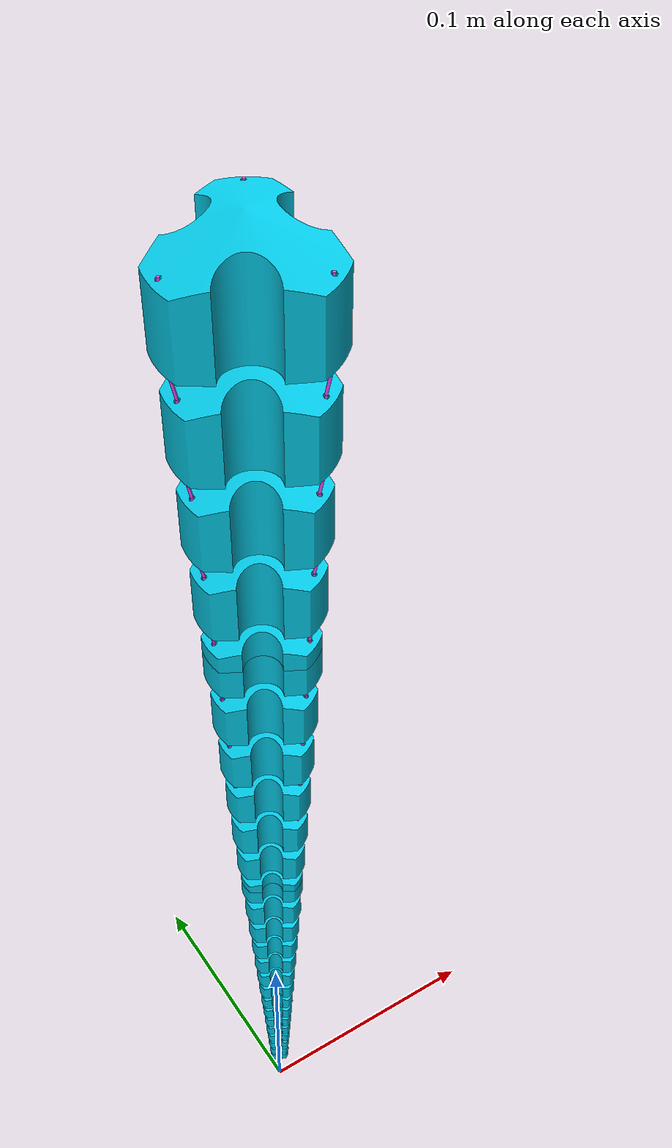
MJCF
<?xml version="1.0" ?>
<!-- Generated using onshape-to-robot -->
<!-- Onshape https://cad.onshape.com/documents/11f47046aadde998d93845f5/w/2219ecd5bc279fe0ecc107c4/e/786bc53f5acd65211f6c0c24 -->
<mujoco model="my-SpiRob">
  <compiler angle="radian" meshdir="assets" autolimits="true"/>
  <default>
    <default class="my-SpiRob">
      <joint frictionloss="0.1" armature="0.005"/>
      <position kp="50" dampratio="1"/>
      <default class="visual">
        <geom type="mesh" contype="0" conaffinity="0" group="2"/>
      </default>
      <default class="collision">
          <geom group="3"
                contype="1"
                conaffinity="1"
                friction="1 0.5 0.1"/>
      </default>
    </default>
  </default>
  <worldbody>

    <!-- Link segment_1__configuration_default -->
    <body name="segment_1__configuration_default" pos="0 0 0.5" euler="0 -1.5708 0" childclass="my-SpiRob">
      <inertial pos="-0.023719 1.84225e-08 1.05571e-08" mass="0.024494" fullinertia="7.0234e-6 5.8528e-6 5.8528e-6 -7.5706e-15 7.9598e-12 -1.1009e-12"/>
      <!-- Part segment_1__configuration_default -->
      <geom type="mesh" class="visual" pos="0 0 0" quat="1 0 0 0" mesh="segment_1__configuration_default" material="segment_1__configuration_default_material"/>
      <geom type="mesh" class="collision" pos="0 0 0" quat="1 0 0 0" mesh="segment_1__configuration_default" material="segment_1__configuration_default_material"/>
      <!-- Frame 1 -->
      <site group="3" name="1" pos="-0.0100544 -5.44356e-20 0.0250952" quat="0.5 0.5 0.5 0.5"/>
      <!-- Frame 2 -->
      <site group="3" name="2" pos="-0.0400151 -5.44356e-20 0.0250952" quat="0.5 0.5 0.5 0.5"/>
      <!-- Frame 3 -->
      <site group="3" name="3" pos="-0.0100552 0.0217331 -0.0125476" quat="0.5 0.5 0.5 0.5"/>
      <!-- Frame 4 -->
      <site group="3" name="4" pos="-0.0400151 0.0217331 -0.0125476" quat="0.5 0.5 0.5 0.5"/>
      <!-- Frame 5 -->
      <site group="3" name="5" pos="-0.040015 -0.0217331 -0.0125476" quat="0.5 0.5 0.5 0.5"/>
      <!-- Frame 6 -->
      <site group="3" name="6" pos="-0.0100551 -0.0217331 -0.0125476" quat="0.5 0.5 0.5 0.5"/>
      <!-- Link segment_2__configuration_default -->
      <body name="segment_2__configuration_default" pos="-0.042844 -1.48645e-19 -8.96728e-22" quat="6.93681e-16 -0 1 8.33698e-16">
        <site name="ee_seg1" pos="0 0 0" rgba="0 1 0 1" size="0.003" group="3"/>  <!-- end of seg2_ -->
        <!-- Joint from segment_1__configuration_default to segment_2__configuration_default -->
        <joint axis="0 0 1" name="x_1" type="hinge" damping="0.1"/>
        <joint axis="0 1 0" name="y_1" type="hinge" damping="0.1"/>
        <inertial pos="0.0218709 1.13482e-08 -5.9967e-09" mass="0.019051" fullinertia="4.6822e-6 4.097e-6 4.097e-6 1.0032e-15 5.326e-12 -6.0313e-13"/>
        <!-- Part segment_2__configuration_default -->
        <geom type="mesh" class="visual" pos="-0.042844 -1.28885e-35 2.62344e-18" quat="9.60979e-18 -0 -1 5.46996e-17" mesh="segment_2__configuration_default" material="segment_2__configuration_default_material"/>
        <geom type="mesh" class="collision" pos="-0.042844 -1.28885e-35 2.62344e-18" quat="9.60979e-18 -0 -1 5.46996e-17" mesh="segment_2__configuration_default" material="segment_2__configuration_default_material"/>
        <!-- Frame 7 -->
        <site group="3" name="7" pos="0.00916355 -0.0198802 0.0114778" quat="0.5 -0.5 -0.5 0.5"/>
        <!-- Frame 8 -->
        <site group="3" name="8" pos="0.00916268 -5.44356e-20 -0.0229556" quat="0.5 -0.5 -0.5 0.5"/>
        <!-- Frame 9 -->
        <site group="3" name="9" pos="0.00916308 0.0198802 0.0114778" quat="0.5 -0.5 -0.5 0.5"/>
        <!-- Frame 10 -->
        <site group="3" name="10" pos="0.036951 0.0198802 0.0114778" quat="0.5 -0.5 -0.5 0.5"/>
        <!-- Frame 11 -->
        <site group="3" name="11" pos="0.036951 -5.44356e-20 -0.0229556" quat="0.5 -0.5 -0.5 0.5"/>
        <!-- Frame 12 -->
        <site group="3" name="12" pos="0.0369508 -0.0198802 0.0114778" quat="0.5 -0.5 -0.5 0.5"/>
        <!-- Link segment_3__configuration_default -->
        <body name="segment_3__configuration_default" pos="0.0395269 2.51311e-19 -2.42033e-18" quat="1 -0 0 7.01374e-19">
          <site name="ee_seg2" pos="0 0 0" rgba="0 1 0 1" size="0.003" group="3"/>  <!-- end of seg3_ -->
          <!-- Joint from segment_2__configuration_default to segment_3__configuration_default -->
          <joint axis="0 0 1" name="x_2" type="hinge" damping="0.1"/>
          <joint axis="0 1 0" name="y_2" type="hinge" damping="0.1"/>
          <inertial pos="0.0201766 1.11039e-08 -5.4109e-09" mass="0.014969" fullinertia="3.219e-6 2.6338e-6 2.6338e-6 4.7817e-15 3.5644e-12 -3.0552e-13"/>
          <!-- Part segment_3__configuration_default -->
          <geom type="mesh" class="visual" pos="-0.0823709 0 5.04376e-18" quat="0 0 1 0" mesh="segment_3__configuration_default" material="segment_3__configuration_default_material"/>
          <geom type="mesh" class="collision" pos="-0.0823709 0 5.04376e-18" quat="0 0 1 0" mesh="segment_3__configuration_default" material="segment_3__configuration_default_material"/>
          <!-- Frame 13 -->
          <site group="3" name="13" pos="0.0341241 0.0181707 0.0104908" quat="0.5 -0.5 -0.5 0.5"/>
          <!-- Frame 14 -->
          <site group="3" name="14" pos="0.00834014 0.0181707 0.0104908" quat="0.5 -0.5 -0.5 0.5"/>
          <!-- Frame 15 -->
          <site group="3" name="15" pos="0.00834105 -0.0181707 0.0104908" quat="0.5 -0.5 -0.5 0.5"/>
          <!-- Frame 16 -->
          <site group="3" name="16" pos="0.0341239 -0.0181707 0.0104908" quat="0.5 -0.5 -0.5 0.5"/>
          <!-- Frame 17 -->
          <site group="3" name="17" pos="0.0341241 -5.44356e-20 -0.0209817" quat="0.5 -0.5 -0.5 0.5"/>
          <!-- Frame 18 -->
          <site group="3" name="18" pos="0.00834012 -5.44356e-20 -0.0209817" quat="0.5 -0.5 -0.5 0.5"/>
          <!-- Link segment_4__configuration_default -->
          <body name="segment_4__configuration_default" pos="0.0364667 3.56718e-18 -2.23294e-18" quat="1 0 -1.11022e-16 8.67362e-19">
            <site name="ee_seg3" pos="0 0 0" rgba="0 1 0 1" size="0.003" group="3"/>  <!-- end of seg4_ -->
            <!-- Joint from segment_3__configuration_default to segment_4__configuration_default -->
            <joint axis="0 0 1" name="x_3" type="hinge" damping="0.1"/>
            <joint axis="0 1 0" name="y_3" type="hinge" damping="0.1"/>
            <inertial pos="0.0186135 1.05568e-08 -1.17938e-08" mass="0.011793" fullinertia="2.0485e-6 1.7558e-6 1.7558e-6 6.6137e-16 2.3909e-12 -1.6841e-13"/>
            <!-- Part segment_4__configuration_default -->
            <geom type="mesh" class="visual" pos="-0.118838 -7.70372e-34 7.2767e-18" quat="0 0 1 0" mesh="segment_4__configuration_default" material="segment_4__configuration_default_material"/>
            <geom type="mesh" class="collision" pos="-0.118838 -7.70372e-34 7.2767e-18" quat="0 0 1 0" mesh="segment_4__configuration_default" material="segment_4__configuration_default_material"/>
            <!-- Frame 19 -->
            <site group="3" name="19" pos="0.00758095 0.0165936 0.0095803" quat="0.5 -0.5 -0.5 0.5"/>
            <!-- Frame 20 -->
            <site group="3" name="20" pos="0.00758153 -5.44356e-20 -0.0191606" quat="0.5 -0.5 -0.5 0.5"/>
            <!-- Frame 21 -->
            <site group="3" name="21" pos="0.00758306 -0.0165936 0.0095803" quat="0.5 -0.5 -0.5 0.5"/>
            <!-- Frame 22 -->
            <site group="3" name="22" pos="0.0315159 -0.0165936 0.0095803" quat="0.5 -0.5 -0.5 0.5"/>
            <!-- Frame 23 -->
            <site group="3" name="23" pos="0.031516 0.0165936 0.0095803" quat="0.5 -0.5 -0.5 0.5"/>
            <!-- Frame 24 -->
            <site group="3" name="24" pos="0.031516 -5.44356e-20 -0.0191606" quat="0.5 -0.5 -0.5 0.5"/>
            <!-- Link segment_5_1__configuration_default -->
            <body name="segment_5_1__configuration_default" pos="0.0336433 -3.46945e-18 -2.06006e-18" quat="1 0 0 0">
              <site name="ee_seg4" pos="0 0 0" rgba="0 1 0 1" size="0.003" group="3"/>  <!-- end of seg5_1_ -->
              <!-- Joint from segment_4__configuration_default to segment_5_1__configuration_default -->
              <joint axis="0 0 1" name="x_4" type="hinge" damping="0.1"/>
              <joint axis="0 1 0" name="y_4" type="hinge" damping="0.1"/>
              <inertial pos="0.0171713 4.27188e-09 -1.04214e-08" mass="0.0090718" fullinertia="1.4632e-6 1.1706e-6 1.1706e-6 -3.4327e-13 3.0317e-14 4.0648e-14"/>
              <!-- Part segment_5_2__configuration_default -->
              <geom type="mesh" class="visual" pos="-0.152481 9.32588e-18 9.33676e-18" quat="3.06162e-17 0 -1 -4.03897e-28" mesh="segment_5_2__configuration_default" material="segment_5_2__configuration_default_material"/>
              <geom type="mesh" class="collision" pos="-0.152481 9.32588e-18 9.33676e-18" quat="3.06162e-17 0 -1 -4.03897e-28" mesh="segment_5_2__configuration_default" material="segment_5_2__configuration_default_material"/>
              <!-- Part segment_5_1__configuration_default -->
              <geom type="mesh" class="visual" pos="-0.152481 -1.09476e-47 9.33676e-18" quat="0 0 1 0" mesh="segment_5_1__configuration_default" material="segment_5_1__configuration_default_material"/>
              <geom type="mesh" class="collision" pos="-0.152481 -1.09476e-47 9.33676e-18" quat="0 0 1 0" mesh="segment_5_1__configuration_default" material="segment_5_1__configuration_default_material"/>
              <!-- Frame 25 -->
              <site group="3" name="25" pos="0.00696165 0.0151386 0.00874025" quat="0.5 -0.5 -0.5 0.5"/>
              <!-- Frame 26 -->
              <site group="3" name="26" pos="0.00696375 -0.0151386 0.00874025" quat="0.5 -0.5 -0.5 0.5"/>
              <!-- Frame 27 -->
              <site group="3" name="27" pos="0.00696158 -5.44356e-20 -0.0174805" quat="0.5 -0.5 -0.5 0.5"/>
              <!-- Frame 28 -->
              <site group="3" name="28" pos="0.0290589 0.0151386 0.00874025" quat="0.5 -0.5 -0.5 0.5"/>
              <!-- Frame 29 -->
              <site group="3" name="29" pos="0.0290589 -8.06032e-19 -0.0174805" quat="0.5 -0.5 -0.5 0.5"/>
              <!-- Frame 30 -->
              <site group="3" name="30" pos="0.0290587 -0.0151386 0.00874025" quat="0.5 -0.5 -0.5 0.5"/>
              <!-- Link segment_6__configuration_default -->
              <body name="segment_6__configuration_default" pos="0.0310386 6.93889e-18 -1.90057e-18" quat="1 0 0 0">
                <site name="ee_seg5" pos="0 0 0" rgba="0 1 0 1" size="0.003" group="3"/>  <!-- end of seg6_ -->
                <!-- Joint from segment_5_1__configuration_default to segment_6__configuration_default -->
                <joint axis="0 0 1" name="x_5" type="hinge" damping="0.1"/>
                <joint axis="0 1 0" name="y_5" type="hinge" damping="0.1"/>
                <inertial pos="0.0158407 9.68272e-09 -2.25308e-08" mass="0.0072575" fullinertia="8.7792e-7 8.7792e-7 8.7792e-7 -6.1279e-14 2.3563e-13 1.9232e-13"/>
                <!-- Part segment_6__configuration_default -->
                <geom type="mesh" class="visual" pos="-0.183519 0 1.12373e-17" quat="0 0 1 0" mesh="segment_6__configuration_default" material="segment_6__configuration_default_material"/>
                <geom type="mesh" class="collision" pos="-0.183519 0 1.12373e-17" quat="0 0 1 0" mesh="segment_6__configuration_default" material="segment_6__configuration_default_material"/>
                <!-- Frame 31 -->
                <site group="3" name="31" pos="0.00623536 0.0137962 0.00796523" quat="0.5 -0.5 -0.5 0.5"/>
                <!-- Frame 32 -->
                <site group="3" name="32" pos="0.00623682 -0.0137962 0.00796523" quat="0.5 -0.5 -0.5 0.5"/>
                <!-- Frame 33 -->
                <site group="3" name="33" pos="0.0062347 -5.44356e-20 -0.0159305" quat="0.5 -0.5 -0.5 0.5"/>
                <!-- Frame 34 -->
                <site group="3" name="34" pos="0.0268901 0.0137962 0.00796523" quat="0.5 -0.5 -0.5 0.5"/>
                <!-- Frame 35 -->
                <site group="3" name="35" pos="0.0268901 -5.44356e-20 -0.0159305" quat="0.5 -0.5 -0.5 0.5"/>
                <!-- Frame 36 -->
                <site group="3" name="36" pos="0.0268899 -0.0137962 0.00796523" quat="0.5 -0.5 -0.5 0.5"/>
                <!-- Link segment_7__configuration_default -->
                <body name="segment_7__configuration_default" pos="0.0286355 3.46945e-17 -1.75342e-18" quat="1 -4.2727e-16 4.44089e-16 -2.83183e-19">
                  <site name="ee_seg6" pos="0 0 0" rgba="0 1 0 1" size="0.003" group="3"/>  <!-- end of seg7_ -->
                  <!-- Joint from segment_6__configuration_default to segment_7__configuration_default -->
                  <joint axis="0 0 1" name="x_6" type="hinge" damping="0.1"/>
                  <joint axis="0 1 0" name="y_6" type="hinge" damping="0.1"/>
                  <inertial pos="0.0146131 9.45033e-09 -2.1313e-08" mass="0.0058967" fullinertia="5.8528e-7 5.8528e-7 5.8528e-7 -4.0121e-14 1.5873e-13 1.5785e-13"/>
                  <!-- Part segment_7__configuration_default -->
                  <geom type="mesh" class="visual" pos="-0.212155 0 1.29907e-17" quat="0 0 1 0" mesh="segment_7__configuration_default" material="segment_7__configuration_default_material"/>
                  <geom type="mesh" class="collision" pos="-0.212155 0 1.29907e-17" quat="0 0 1 0" mesh="segment_7__configuration_default" material="segment_7__configuration_default_material"/>
                  <!-- Frame 37 -->
                  <site group="3" name="37" pos="0.00564008 0.0125577 0.00725022" quat="0.5 -0.5 -0.5 0.5"/>
                  <!-- Frame 38 -->
                  <site group="3" name="38" pos="0.00563888 -5.44356e-20 -0.0145004" quat="0.5 -0.5 -0.5 0.5"/>
                  <!-- Frame 39 -->
                  <site group="3" name="39" pos="0.00564067 -0.0125577 0.00725022" quat="0.5 -0.5 -0.5 0.5"/>
                  <!-- Frame 40 -->
                  <site group="3" name="40" pos="0.0248419 -0.0125577 0.00725022" quat="0.5 -0.5 -0.5 0.5"/>
                  <!-- Frame 41 -->
                  <site group="3" name="41" pos="0.0248421 0.0125577 0.00725022" quat="0.5 -0.5 -0.5 0.5"/>
                  <!-- Frame 42 -->
                  <site group="3" name="42" pos="0.0248421 -5.44356e-20 -0.0145004" quat="0.5 -0.5 -0.5 0.5"/>
                  <!-- Link segment_8__configuration_default -->
                  <body name="segment_8__configuration_default" pos="0.0264185 4.19961e-17 -1.61767e-18" quat="1 -0 1.249e-16 1.25123e-18">
                    <site name="ee_seg7" pos="0 0 0" rgba="0 1 0 1" size="0.003" group="3"/>  <!-- end of seg8_ -->
                    <!-- Joint from segment_7__configuration_default to segment_8__configuration_default -->
                    <joint axis="0 0 1" name="x_7" type="hinge" damping="0.1"/>
                    <joint axis="0 1 0" name="y_7" type="hinge" damping="0.1"/>
                    <inertial pos="0.0134806 9.2626e-09 -2.02192e-08" mass="0.0045359" fullinertia="2.9264e-7 2.9264e-7 2.9264e-7 -2.6276e-14 1.0702e-13 1.2715e-13"/>
                    <!-- Part segment_8__configuration_default -->
                    <geom type="mesh" class="visual" pos="-0.238574 -3.62701e-19 1.46084e-17" quat="0 0 1 0" mesh="segment_8__configuration_default" material="segment_8__configuration_default_material"/>
                    <geom type="mesh" class="collision" pos="-0.238574 -3.62701e-19 1.46084e-17" quat="0 0 1 0" mesh="segment_8__configuration_default" material="segment_8__configuration_default_material"/>
                    <!-- Frame 43 -->
                    <site group="3" name="43" pos="0.0229527 -4.17137e-19 -0.0131811" quat="0.5 -0.5 -0.5 0.5"/>
                    <!-- Frame 44 -->
                    <site group="3" name="44" pos="0.00508945 -4.17137e-19 -0.0131811" quat="0.5 -0.5 -0.5 0.5"/>
                    <!-- Frame 45 -->
                    <site group="3" name="45" pos="0.00509111 0.0114152 0.00659057" quat="0.5 -0.5 -0.5 0.5"/>
                    <!-- Frame 46 -->
                    <site group="3" name="46" pos="0.0229527 0.0114152 0.00659057" quat="0.5 -0.5 -0.5 0.5"/>
                    <!-- Frame 47 -->
                    <site group="3" name="47" pos="0.0229525 -0.0114152 0.00659057" quat="0.5 -0.5 -0.5 0.5"/>
                    <!-- Frame 48 -->
                    <site group="3" name="48" pos="0.00509068 -0.0114152 0.00659057" quat="0.5 -0.5 -0.5 0.5"/>
                    <!-- Link segment_9__configuration_default -->
                    <body name="segment_9__configuration_default" pos="0.0243731 2.92174e-17 -1.49242e-18" quat="1 -4.99676e-16 3.33067e-16 3.44807e-18">
                      <site name="ee_seg8" pos="0 0 0" rgba="0 1 0 1" size="0.003" group="3"/>  <!-- end of seg9_ -->
                      <!-- Joint from segment_8__configuration_default to segment_9__configuration_default -->
                      <joint axis="0 0 1" name="x_8" type="hinge" damping="0.1"/>
                      <joint axis="0 1 0" name="y_8" type="hinge" damping="0.1"/>
                      <inertial pos="0.0124357 9.25317e-09 -1.95027e-08" mass="0.0036287" fullinertia="2.9264e-7 2.9264e-7 2.9264e-7 -1.5109e-14 7.0087e-14 1.2238e-13"/>
                      <!-- Part segment_9__configuration_default -->
                      <geom type="mesh" class="visual" pos="-0.262947 1.2326e-32 1.61008e-17" quat="3.06162e-17 -0 -1 6.37496e-17" mesh="segment_9__configuration_default" material="segment_9__configuration_default_material"/>
                      <geom type="mesh" class="collision" pos="-0.262947 1.2326e-32 1.61008e-17" quat="3.06162e-17 -0 -1 6.37496e-17" mesh="segment_9__configuration_default" material="segment_9__configuration_default_material"/>
                      <!-- Frame 49 -->
                      <site group="3" name="49" pos="0.0212094 -0.0103611 0.00598198" quat="0.5 -0.5 -0.5 0.5"/>
                      <!-- Frame 50 -->
                      <site group="3" name="50" pos="0.0045823 -0.0103611 0.00598198" quat="0.5 -0.5 -0.5 0.5"/>
                      <!-- Frame 52 -->
                      <site group="3" name="52" pos="0.0212096 0.0103611 0.00598198" quat="0.5 -0.5 -0.5 0.5"/>
                      <!-- Frame 53 -->
                      <site group="3" name="53" pos="0.00458299 0.0103611 0.00598198" quat="0.5 -0.5 -0.5 0.5"/>
                      <!-- Frame 54 -->
                      <site group="3" name="54" pos="0.00458181 -5.44356e-20 -0.011964" quat="0.5 -0.5 -0.5 0.5"/>
                      <!-- Frame 55 -->
                      <site group="3" name="55" pos="0.0212095 -5.44356e-20 -0.011964" quat="0.5 -0.5 -0.5 0.5"/>
                      <!-- Link segment_10__configuration_default -->
                      <body name="segment_10__configuration_default" pos="0.0224861 -1.98059e-18 -1.37688e-18" quat="1 0 1.11022e-16 -1.0641e-17">
                        <site name="ee_seg9" pos="0 0 0" rgba="0 1 0 1" size="0.003" group="3"/>  <!-- end of seg10_ -->
                        <!-- Joint from segment_9__configuration_default to segment_10__configuration_default -->
                        <joint axis="0 0 1" name="x_9" type="hinge" damping="0.1"/>
                        <joint axis="0 1 0" name="y_9" type="hinge" damping="0.1"/>
                        <inertial pos="0.0114718 1.09038e-08 -1.15964e-08" mass="0.0027216" fullinertia="2.9264e-7 2.9264e-7 2.9264e-7 -9.9907e-15 4.7291e-14 9.3645e-14"/>
                        <!-- Part segment_10__configuration_default -->
                        <geom type="mesh" class="visual" pos="-0.285433 -1.2326e-32 1.74777e-17" quat="0 0 1 0" mesh="segment_10__configuration_default" material="segment_10__configuration_default_material"/>
                        <geom type="mesh" class="collision" pos="-0.285433 -1.2326e-32 1.74777e-17" quat="0 0 1 0" mesh="segment_10__configuration_default" material="segment_10__configuration_default_material"/>
                        <!-- Frame 51 -->
                        <site group="3" name="51" pos="0.0196014 -5.44356e-20 -0.010841" quat="0.5 -0.5 -0.5 0.5"/>
                        <!-- Frame 56 -->
                        <site group="3" name="56" pos="0.00411437 0.00938862 0.00542052" quat="0.5 -0.5 -0.5 0.5"/>
                        <!-- Frame 57 -->
                        <site group="3" name="57" pos="0.00411352 -5.44356e-20 -0.010841" quat="0.5 -0.5 -0.5 0.5"/>
                        <!-- Frame 58 -->
                        <site group="3" name="58" pos="0.00411448 -0.00938862 0.00542052" quat="0.5 -0.5 -0.5 0.5"/>
                        <!-- Frame 59 -->
                        <site group="3" name="59" pos="0.0196013 0.00938862 0.00542052" quat="0.5 -0.5 -0.5 0.5"/>
                        <!-- Frame 60 -->
                        <site group="3" name="60" pos="0.0196012 -0.00938862 0.00542052" quat="0.5 -0.5 -0.5 0.5"/>
                        <!-- Link segment_11_2__configuration_default -->
                        <body name="segment_11_2__configuration_default" pos="0.0207452 5.55112e-17 -1.27028e-18" quat="1 5.51286e-16 0 -2.11798e-17">
                          <site name="ee_seg10" pos="0 0 0" rgba="0 1 0 1" size="0.003" group="3"/>  <!-- end of seg11_2_ -->
                          <!-- Joint from segment_10__configuration_default to segment_11_2__configuration_default -->
                          <joint axis="0 0 1" name="x_10" type="hinge" damping="0.1"/>
                          <joint axis="0 1 0" name="y_10" type="hinge" damping="0.1"/>
                          <inertial pos="0.0105825 4.66794e-09 -4.96433e-09" mass="0.002268" fullinertia="1.2092e-7 1.0324e-7 1.0324e-7 -3.7487e-14 1.628e-15 2.4836e-14"/>
                          <!-- Part segmentt_11_1__configuration_default -->
                          <geom type="mesh" class="visual" pos="-0.306178 0 1.8748e-17" quat="0 0 1 0" mesh="segmentt_11_1__configuration_default" material="segmentt_11_1__configuration_default_material"/>
                          <geom type="mesh" class="collision" pos="-0.306178 0 1.8748e-17" quat="0 0 1 0" mesh="segmentt_11_1__configuration_default" material="segmentt_11_1__configuration_default_material"/>
                          <!-- Part segment_11_2__configuration_default -->
                          <geom type="mesh" class="visual" pos="-0.306178 0 1.8748e-17" quat="3.30788e-17 0 -1 4.19873e-17" mesh="segment_11_2__configuration_default" material="segment_11_2__configuration_default_material"/>
                          <geom type="mesh" class="collision" pos="-0.306178 0 1.8748e-17" quat="3.30788e-17 0 -1 4.19873e-17" mesh="segment_11_2__configuration_default" material="segment_11_2__configuration_default_material"/>
                          <!-- Frame 61 -->
                          <site group="3" name="61" pos="0.0180827 -0.00849142 0.00490253" quat="0.5 -0.5 -0.5 0.5"/>
                          <!-- Frame 62 -->
                          <site group="3" name="62" pos="0.00373368 -0.00849142 0.00490253" quat="0.5 -0.5 -0.5 0.5"/>
                          <!-- Frame 63 -->
                          <site group="3" name="63" pos="0.00373261 -5.44356e-20 -0.00980505" quat="0.5 -0.5 -0.5 0.5"/>
                          <!-- Frame 64 -->
                          <site group="3" name="64" pos="0.0180829 -5.44356e-20 -0.00980505" quat="0.5 -0.5 -0.5 0.5"/>
                          <!-- Frame 65 -->
                          <site group="3" name="65" pos="0.0180829 0.00849142 0.00490253" quat="0.5 -0.5 -0.5 0.5"/>
                          <!-- Frame 66 -->
                          <site group="3" name="66" pos="0.00373294 0.00849142 0.00490253" quat="0.5 -0.5 -0.5 0.5"/>
                          <!-- Link segment_12__configuration_default -->
                          <body name="segment_12__configuration_default" pos="0.019139 5.55112e-17 -1.17193e-18" quat="1 4.52636e-16 -4.44089e-16 2.54034e-29">
                            <site name="ee_seg11" pos="0 0 0" rgba="0 1 0 1" size="0.003" group="3"/>  <!-- end of seg12_ -->
                            <!-- Joint from segment_11_2__configuration_default to segment_12__configuration_default -->
                            <joint axis="0 0 1" name="x_11" type="hinge" damping="0.1"/>
                            <joint axis="0 1 0" name="y_11" type="hinge" damping="0.1"/>
                            <inertial pos="0.00976212 9.31267e-09 -1.61388e-08" mass="0.0018144" fullinertia="8.0213e-8 6.8624e-8 6.8624e-8 -5.607e-15 2.0444e-14 5.0451e-14"/>
                            <!-- Part segment_12__configuration_default -->
                            <geom type="mesh" class="visual" pos="-0.325317 0 1.99199e-17" quat="0 0 1 0" mesh="segment_12__configuration_default" material="segment_12__configuration_default_material"/>
                            <geom type="mesh" class="collision" pos="-0.325317 0 1.99199e-17" quat="0 0 1 0" mesh="segment_12__configuration_default" material="segment_12__configuration_default_material"/>
                            <!-- Frame 67 -->
                            <site group="3" name="67" pos="0.0167487 -0.00766369 0.00442464" quat="0.5 -0.5 -0.5 0.5"/>
                            <!-- Frame 68 -->
                            <site group="3" name="68" pos="0.00328566 -0.00766369 0.00442464" quat="0.5 -0.5 -0.5 0.5"/>
                            <!-- Frame 69 -->
                            <site group="3" name="69" pos="0.0167489 0.00766369 0.00442464" quat="0.5 -0.5 -0.5 0.5"/>
                            <!-- Frame 70 -->
                            <site group="3" name="70" pos="0.00328347 0.00766369 0.00442464" quat="0.5 -0.5 -0.5 0.5"/>
                            <!-- Frame 71 -->
                            <site group="3" name="71" pos="0.0167489 -5.44356e-20 -0.00884927" quat="0.5 -0.5 -0.5 0.5"/>
                            <!-- Frame 72 -->
                            <site group="3" name="72" pos="0.00328429 -5.44356e-20 -0.00884927" quat="0.5 -0.5 -0.5 0.5"/>
                            <!-- Link segment_13__configuration_default -->
                            <body name="segment_13__configuration_default" pos="0.0176573 2.46519e-32 -1.0812e-18" quat="1 -0 -1.11022e-15 -8.69362e-26">
                              <site name="ee_seg12" pos="0 0 0" rgba="0 1 0 1" size="0.003" group="3"/>  <!-- end of seg13_ -->
                              <!-- Joint from segment_12__configuration_default to segment_13__configuration_default -->
                              <joint axis="0 0 1" name="x_12" type="hinge" damping="0.1"/>
                              <joint axis="0 1 0" name="y_12" type="hinge" damping="0.1"/>
                              <inertial pos="0.00900538 9.25531e-09 -1.56183e-08" mass="0.0013608" fullinertia="5.3173e-8 4.5564e-8 4.5564e-8 -3.8189e-15 1.3915e-14 3.8628e-14"/>
                              <!-- Part segment_13__configuration_default -->
                              <geom type="mesh" class="visual" pos="-0.342974 0 2.10011e-17" quat="3.44552e-17 -0 -1 -1.11022e-16" mesh="segment_13__configuration_default" material="segment_13__configuration_default_material"/>
                              <geom type="mesh" class="collision" pos="-0.342974 0 2.10011e-17" quat="3.44552e-17 -0 -1 -1.11022e-16" mesh="segment_13__configuration_default" material="segment_13__configuration_default_material"/>
                              <!-- Frame 73 -->
                              <site group="3" name="73" pos="0.0154859 -0.00690005 0.00398375" quat="0.5 -0.5 -0.5 0.5"/>
                              <!-- Frame 74 -->
                              <site group="3" name="74" pos="0.0029181 -0.00690005 0.00398375" quat="0.5 -0.5 -0.5 0.5"/>
                              <!-- Frame 75 -->
                              <site group="3" name="75" pos="0.00291607 -5.44356e-20 -0.00796749" quat="0.5 -0.5 -0.5 0.5"/>
                              <!-- Frame 76 -->
                              <site group="3" name="76" pos="0.0154861 -5.44356e-20 -0.00796749" quat="0.5 -0.5 -0.5 0.5"/>
                              <!-- Frame 77 -->
                              <site group="3" name="77" pos="0.0154861 0.00690005 0.00398375" quat="0.5 -0.5 -0.5 0.5"/>
                              <!-- Frame 78 -->
                              <site group="3" name="78" pos="0.00291581 0.00690005 0.00398375" quat="0.5 -0.5 -0.5 0.5"/>
                              <!-- Link segment_14__configuration_default -->
                              <body name="segment_14__configuration_default" pos="0.0162902 2.4929e-18 -9.97487e-19" quat="1 -0 -1.11022e-16 6.53517e-19">
                                <site name="ee_seg13" pos="0 0 0" rgba="0 1 0 1" size="0.003" group="3"/>  <!-- end of seg14_ -->
                                <!-- Joint from segment_13__configuration_default to segment_14__configuration_default -->
                                <joint axis="0 0 1" name="x_13" type="hinge" damping="0.1"/>
                                <joint axis="0 1 0" name="y_13" type="hinge" damping="0.1"/>
                                <inertial pos="0.00830739 9.27243e-09 -1.52171e-08" mass="0.00090718" fullinertia="3.5205e-8 3.02e-8 3.02e-8 -2.6352e-15 9.4932e-15 2.9527e-14"/>
                                <!-- Part segment_14__configuration_default -->
                                <geom type="mesh" class="visual" pos="-0.359264 0 2.19986e-17" quat="3.06162e-17 -0 -1 3.49785e-17" mesh="segment_14__configuration_default" material="segment_14__configuration_default_material"/>
                                <geom type="mesh" class="collision" pos="-0.359264 0 2.19986e-17" quat="3.06162e-17 -0 -1 3.49785e-17" mesh="segment_14__configuration_default" material="segment_14__configuration_default_material"/>
                                <!-- Frame 79 -->
                                <site group="3" name="79" pos="0.00257692 0.00619553 0.00357699" quat="0.5 -0.5 -0.5 0.5"/>
                                <!-- Frame 80 -->
                                <site group="3" name="80" pos="0.0143211 0.00619553 0.00357699" quat="0.5 -0.5 -0.5 0.5"/>
                                <!-- Frame 81 -->
                                <site group="3" name="81" pos="0.0143209 -0.00619553 0.00357699" quat="0.5 -0.5 -0.5 0.5"/>
                                <!-- Frame 82 -->
                                <site group="3" name="82" pos="0.00257885 -0.00619553 0.00357699" quat="0.5 -0.5 -0.5 0.5"/>
                                <!-- Frame 83 -->
                                <site group="3" name="83" pos="0.00257673 -5.44356e-20 -0.00715398" quat="0.5 -0.5 -0.5 0.5"/>
                                <!-- Frame 84 -->
                                <site group="3" name="84" pos="0.0143211 -5.44356e-20 -0.00715398" quat="0.5 -0.5 -0.5 0.5"/>
                                <!-- Link segment_15__configuration_default -->
                                <body name="segment_15__configuration_default" pos="0.015029 -1.40093e-19 -9.20259e-19" quat="1 0 -1.11022e-16 -3.46945e-18">
                                  <site name="ee_seg14" pos="0 0 0" rgba="0 1 0 1" size="0.003" group="3"/>  <!-- end of seg15_ -->
                                  <!-- Joint from segment_14__configuration_default to segment_15__configuration_default -->
                                  <joint axis="0 0 1" name="x_14" type="hinge" damping="0.1"/>
                                  <joint axis="0 1 0" name="y_14" type="hinge" damping="0.1"/>
                                  <inertial pos="0.00766367 9.36767e-09 -1.49414e-08" mass="0.00090718" fullinertia="2.3285e-8 2.0017e-8 2.0017e-8 -1.4878e-15 6.0489e-15 2.2852e-14"/>
                                  <!-- Part segment_15__configuration_default -->
                                  <geom type="mesh" class="visual" pos="-0.374293 1.40093e-19 2.29189e-17" quat="3.24416e-17 -0 -1 -1.11022e-16" mesh="segment_15__configuration_default" material="segment_15__configuration_default_material"/>
                                  <geom type="mesh" class="collision" pos="-0.374293 1.40093e-19 2.29189e-17" quat="3.24416e-17 -0 -1 -1.11022e-16" mesh="segment_15__configuration_default" material="segment_15__configuration_default_material"/>
                                  <!-- Frame 85 -->
                                  <site group="3" name="85" pos="0.0132462 8.56574e-20 -0.00640345" quat="0.5 -0.5 -0.5 0.5"/>
                                  <!-- Frame 86 -->
                                  <site group="3" name="86" pos="0.00226401 8.56574e-20 -0.00640345" quat="0.5 -0.5 -0.5 0.5"/>
                                  <!-- Frame 87 -->
                                  <site group="3" name="87" pos="0.00226454 0.00554555 0.00320173" quat="0.5 -0.5 -0.5 0.5"/>
                                  <!-- Frame 88 -->
                                  <site group="3" name="88" pos="0.0132462 0.00554555 0.00320173" quat="0.5 -0.5 -0.5 0.5"/>
                                  <!-- Frame 89 -->
                                  <site group="3" name="89" pos="0.0132461 -0.00554555 0.00320173" quat="0.5 -0.5 -0.5 0.5"/>
                                  <!-- Frame 90 -->
                                  <site group="3" name="90" pos="0.00226586 -0.00554555 0.00320173" quat="0.5 -0.5 -0.5 0.5"/>
                                  <!-- Link segment_16__configuration_default -->
                                  <body name="segment_16__configuration_default" pos="0.0138654 -5.79682e-17 -8.49011e-19" quat="1 0 2.22045e-16 -2.66107e-27">
                                    <site name="ee_seg15" pos="0 0 0" rgba="0 1 0 1" size="0.003" group="3"/>  <!-- end of seg16_ -->
                                    <!-- Joint from segment_15__configuration_default to segment_16__configuration_default -->
                                    <joint axis="0 0 1" name="x_15" type="hinge" damping="0.1"/>
                                    <joint axis="0 1 0" name="y_15" type="hinge" damping="0.1"/>
                                    <inertial pos="0.0070701 9.54699e-09 -1.48007e-08" mass="0.00045359" fullinertia="1.5381e-8 1.3242e-8 1.3242e-8 -1.0237e-15 4.0882e-15 1.7441e-14"/>
                                    <!-- Part segment_16__configuration_default -->
                                    <geom type="mesh" class="visual" pos="-0.388159 -2.46519e-32 2.37679e-17" quat="0 0 1 0" mesh="segment_16__configuration_default" material="segment_16__configuration_default_material"/>
                                    <geom type="mesh" class="collision" pos="-0.388159 -2.46519e-32 2.37679e-17" quat="0 0 1 0" mesh="segment_16__configuration_default" material="segment_16__configuration_default_material"/>
                                    <!-- Frame 91 -->
                                    <site group="3" name="91" pos="0.00197662 0.0049459 0.00285551" quat="0.5 -0.5 -0.5 0.5"/>
                                    <!-- Frame 92 -->
                                    <site group="3" name="92" pos="0.0019771 -0.0049459 0.00285551" quat="0.5 -0.5 -0.5 0.5"/>
                                    <!-- Frame 93 -->
                                    <site group="3" name="93" pos="0.0122546 0.0049459 0.00285551" quat="0.5 -0.5 -0.5 0.5"/>
                                    <!-- Frame 94 -->
                                    <site group="3" name="94" pos="0.0122544 -0.0049459 0.00285551" quat="0.5 -0.5 -0.5 0.5"/>
                                    <!-- Frame 95 -->
                                    <site group="3" name="95" pos="0.0122546 -5.44356e-20 -0.00571103" quat="0.5 -0.5 -0.5 0.5"/>
                                    <!-- Frame 96 -->
                                    <site group="3" name="96" pos="0.00197584 -5.44356e-20 -0.00571103" quat="0.5 -0.5 -0.5 0.5"/>
                                    <!-- Link segment_17__configuration_default -->
                                    <body name="segment_17__configuration_default" pos="0.0127919 7.39557e-32 -7.83279e-19" quat="1 1.00791e-16 1.11022e-16 2.76101e-30">
                                      <site name="ee_seg16" pos="0 0 0" rgba="0 1 0 1" size="0.003" group="3"/>  <!-- end of seg17_ -->
                                      <!-- Joint from segment_16__configuration_default to segment_17__configuration_default -->
                                      <joint axis="0 0 1" name="x_16" type="hinge" damping="0.1"/>
                                      <joint axis="0 1 0" name="y_16" type="hinge" damping="0.1"/>
                                      <inertial pos="0.00652292 9.81916e-09 -1.48077e-08" mass="0.00045359" fullinertia="1.0143e-8 8.747e-9 8.747e-9 -7.1814e-16 2.7654e-15 1.3327e-14"/>
                                      <!-- Part segment_17__configuration_default -->
                                      <geom type="mesh" class="visual" pos="-0.400951 0 2.45512e-17" quat="3.44552e-17 -0 -1 -1.11022e-16" mesh="segment_17__configuration_default" material="segment_17__configuration_default_material"/>
                                      <geom type="mesh" class="collision" pos="-0.400951 0 2.45512e-17" quat="3.44552e-17 -0 -1 -1.11022e-16" mesh="segment_17__configuration_default" material="segment_17__configuration_default_material"/>
                                      <!-- Frame 97 -->
                                      <site group="3" name="97" pos="0.00170936 -5.44356e-20 -0.00507222" quat="0.5 -0.5 -0.5 0.5"/>
                                      <!-- Frame 98 -->
                                      <site group="3" name="98" pos="0.00171125 0.00439267 0.00253611" quat="0.5 -0.5 -0.5 0.5"/>
                                      <!-- Frame 99 -->
                                      <site group="3" name="99" pos="0.00171068 -0.00439267 0.00253611" quat="0.5 -0.5 -0.5 0.5"/>
                                      <!-- Frame 100 -->
                                      <site group="3" name="100" pos="0.0113398 0.00439267 0.00253611" quat="0.5 -0.5 -0.5 0.5"/>
                                      <!-- Frame 101 -->
                                      <site group="3" name="101" pos="0.0113397 -5.44356e-20 -0.00507222" quat="0.5 -0.5 -0.5 0.5"/>
                                      <!-- Frame 102 -->
                                      <site group="3" name="102" pos="0.0113396 -0.00439267 0.00253611" quat="0.5 -0.5 -0.5 0.5"/>
                                      <!-- Link segment_18__configuration_default -->
                                      <body name="segment_18__configuration_default" pos="0.0118015 0 -7.22636e-19" quat="1 3.52658e-16 0 -6.97554e-17">
                                        <site name="ee_seg17" pos="0 0 0" rgba="0 1 0 1" size="0.003" group="3"/>  <!-- end of seg18_ -->
                                        <!-- Joint from segment_17__configuration_default to segment_18__configuration_default -->
                                        <joint axis="0 0 1" name="x_17" type="hinge" damping="0.1"/>
                                        <joint axis="0 1 0" name="y_17" type="hinge" damping="0.1"/>
                                        <inertial pos="0.00601868 1.12794e-08 -1.49464e-08" mass="0.00045359" fullinertia="6.681e-9 5.7679e-9 5.7679e-9 -5.8323e-16 1.7813e-15 1.0913e-14"/>
                                        <!-- Part segment_18__configuration_default -->
                                        <geom type="mesh" class="visual" pos="-0.412752 0 2.52738e-17" quat="2.93883e-17 -0 -1 1.97215e-31" mesh="segment_18__configuration_default" material="segment_18__configuration_default_material"/>
                                        <geom type="mesh" class="collision" pos="-0.412752 0 2.52738e-17" quat="2.93883e-17 -0 -1 1.97215e-31" mesh="segment_18__configuration_default" material="segment_18__configuration_default_material"/>
                                        <!-- Frame 103 -->
                                        <site group="3" name="103" pos="0.00146467 -0.00388227 0.00224143" quat="0.5 -0.5 -0.5 0.5"/>
                                        <!-- Frame 104 -->
                                        <site group="3" name="104" pos="0.00146533 0.00388227 0.00224143" quat="0.5 -0.5 -0.5 0.5"/>
                                        <!-- Frame 105 -->
                                        <site group="3" name="105" pos="0.00146395 -5.44356e-20 -0.00448286" quat="0.5 -0.5 -0.5 0.5"/>
                                        <!-- Frame 106 -->
                                        <site group="3" name="106" pos="0.0104957 -5.44356e-20 -0.00448286" quat="0.5 -0.5 -0.5 0.5"/>
                                        <!-- Frame 107 -->
                                        <site group="3" name="107" pos="0.0104958 0.00388227 0.00224143" quat="0.5 -0.5 -0.5 0.5"/>
                                        <!-- Frame 108 -->
                                        <site group="3" name="108" pos="0.0104956 -0.00388227 0.00224143" quat="0.5 -0.5 -0.5 0.5"/>
                                        <!-- Link segment_19__configuration_default -->
                                        <body name="segment_19__configuration_default" pos="0.0108878 2.93959e-18 -6.66688e-19" quat="1 3.70179e-16 -2.22045e-16 3.46945e-18">
                                          <site name="ee_seg18" pos="0 0 0" rgba="0 1 0 1" size="0.003" group="3"/>  <!-- end of seg19_ -->
                                          <!-- Joint from segment_18__configuration_default to segment_19__configuration_default -->
                                          <joint axis="0 0 1" name="x_18" type="hinge" damping="0.1"/>
                                          <joint axis="0 1 0" name="y_18" type="hinge" damping="0.1"/>
                                          <inertial pos="0.00555715 7.27659e-09 -6.67771e-09" mass="0.00045359" fullinertia="4.8959e-9 4.1526e-9 4.1526e-9 -6.0576e-16 1.2578e-15 -1.4134e-15"/>
                                          <!-- Part segment_19__configuration_default -->
                                          <geom type="mesh" class="visual" pos="-0.42364 0 2.59405e-17" quat="0 0 1 0" mesh="segment_19__configuration_default" material="segment_19__configuration_default_material"/>
                                          <geom type="mesh" class="collision" pos="-0.42364 0 2.59405e-17" quat="0 0 1 0" mesh="segment_19__configuration_default" material="segment_19__configuration_default_material"/>
                                          <!-- Frame 109 -->
                                          <site group="3" name="109" pos="0.00134585 0.00341139 0.00196957" quat="0.5 -0.5 -0.5 0.5"/>
                                          <!-- Frame 110 -->
                                          <site group="3" name="110" pos="0.00134619 2.72178e-19 -0.00393914" quat="0.5 -0.5 -0.5 0.5"/>
                                          <!-- Frame 111 -->
                                          <site group="3" name="111" pos="0.0013471 -0.00341139 0.00196957" quat="0.5 -0.5 -0.5 0.5"/>
                                          <!-- Frame 112 -->
                                          <site group="3" name="112" pos="0.0096843 -0.00341139 0.00196957" quat="0.5 -0.5 -0.5 0.5"/>
                                          <!-- Frame 113 -->
                                          <site group="3" name="113" pos="0.00968426 0.00341139 0.00196957" quat="0.5 -0.5 -0.5 0.5"/>
                                          <!-- Frame 114 -->
                                          <site group="3" name="114" pos="0.00968438 2.72178e-19 -0.00393914" quat="0.5 -0.5 -0.5 0.5"/>
                                          <!-- Link segment_20__configuration_default -->
                                          <body name="segment_20__configuration_default" pos="0.0100449 -5.85204e-17 -6.15071e-19" quat="1 -0 -6.66134e-16 -3.46945e-18">
                                            <site name="ee_seg19" pos="0 0 0" rgba="0 1 0 1" size="0.003" group="3"/>  <!-- end of seg20_ -->
                                            <!-- Joint from segment_19__configuration_default to segment_20__configuration_default -->
                                            <joint axis="0 0 1" name="x_19" type="hinge" damping="0.1"/>
                                            <joint axis="0 1 0" name="y_19" type="hinge" damping="0.1"/>
                                            <inertial pos="0.0051282 3.50084e-09 -8.91244e-09" mass="0.00045359" fullinertia="3.26e-9 2.7657e-9 2.7657e-9 -3.4707e-16 6.9385e-16 7.6906e-16"/>
                                            <!-- Part segment_20__configuration_default -->
                                            <geom type="mesh" class="visual" pos="-0.433685 1.2326e-32 2.65555e-17" quat="0 0 1 0" mesh="segment_20__configuration_default" material="segment_20__configuration_default_material"/>
                                            <geom type="mesh" class="collision" pos="-0.433685 1.2326e-32 2.65555e-17" quat="0 0 1 0" mesh="segment_20__configuration_default" material="segment_20__configuration_default_material"/>
                                            <!-- Frame 115 -->
                                            <site group="3" name="115" pos="0.00113692 2.72178e-19 -0.00343751" quat="0.5 -0.5 -0.5 0.5"/>
                                            <!-- Frame 116 -->
                                            <site group="3" name="116" pos="0.00113693 0.00297697 0.00171875" quat="0.5 -0.5 -0.5 0.5"/>
                                            <!-- Frame 117 -->
                                            <site group="3" name="117" pos="0.00113833 -0.00297697 0.00171875" quat="0.5 -0.5 -0.5 0.5"/>
                                            <!-- Frame 118 -->
                                            <site group="3" name="118" pos="0.00896592 -0.00297697 0.00171875" quat="0.5 -0.5 -0.5 0.5"/>
                                            <!-- Frame 119 -->
                                            <site group="3" name="119" pos="0.00896592 0.00297697 0.00171875" quat="0.5 -0.5 -0.5 0.5"/>
                                            <!-- Frame 120 -->
                                            <site group="3" name="120" pos="0.00896601 2.72178e-19 -0.00343751" quat="0.5 -0.5 -0.5 0.5"/>
                                            <!-- Link segment_21__configuration_default -->
                                            <body name="segment_21__configuration_default" pos="0.00926718 5.55112e-17 -5.67451e-19" quat="1 -5.65017e-16 -7.77156e-16 -1.75852e-27">
                                              <site name="ee_seg20" pos="0 0 0" rgba="0 1 0 1" size="0.003" group="3"/>  <!-- end of seg21_ -->
                                              <!-- Joint from segment_20__configuration_default to segment_21__configuration_default -->
                                              <joint axis="0 0 1" name="x_20" type="hinge" damping="0.1"/>
                                              <joint axis="0 1 0" name="y_20" type="hinge" damping="0.1"/>
                                              <inertial pos="0.0047331 3.56445e-09 -8.81065e-09" mass="0.00018915" fullinertia="2.1708e-9 1.8407e-9 1.8407e-9 -2.5223e-16 4.6003e-16 6.2771e-16"/>
                                              <!-- Part segment_21__configuration_default -->
                                              <geom type="mesh" class="visual" pos="-0.442952 -2.46519e-32 2.7123e-17" quat="0 0 1 0" mesh="segment_21__configuration_default" material="segment_21__configuration_default_material"/>
                                              <geom type="mesh" class="collision" pos="-0.442952 -2.46519e-32 2.7123e-17" quat="0 0 1 0" mesh="segment_21__configuration_default" material="segment_21__configuration_default_material"/>
                                              <!-- Frame 121 -->
                                              <site group="3" name="121" pos="0.000945399 -0.00257618 0.00148736" quat="0.5 -0.5 -0.5 0.5"/>
                                              <!-- Frame 122 -->
                                              <site group="3" name="122" pos="0.000944099 0.00257618 0.00148736" quat="0.5 -0.5 -0.5 0.5"/>
                                              <!-- Frame 123 -->
                                              <site group="3" name="123" pos="0.000943825 2.72178e-19 -0.00297472" quat="0.5 -0.5 -0.5 0.5"/>
                                              <!-- Frame 124 -->
                                              <site group="3" name="124" pos="0.00830316 -0.00257618 0.00148736" quat="0.5 -0.5 -0.5 0.5"/>
                                              <!-- Frame 125 -->
                                              <site group="3" name="125" pos="0.00830327 2.72178e-19 -0.00297472" quat="0.5 -0.5 -0.5 0.5"/>
                                              <!-- Frame 126 -->
                                              <site group="3" name="126" pos="0.00830319 0.00257618 0.00148736" quat="0.5 -0.5 -0.5 0.5"/>
                                              <!-- Link segment_22__configuration_default -->
                                              <body name="segment_22__configuration_default" pos="0.00854969 -3.13292e-18 -5.23518e-19" quat="1 -0 1.11022e-16 -1.84596e-16">
                                                <site name="ee_seg21" pos="0 0 0" rgba="0 1 0 1" size="0.003" group="3"/>  <!-- end of seg22_ -->
                                                <!-- Joint from segment_21__configuration_default to segment_22__configuration_default -->
                                                <joint axis="0 0 1" name="x_21" type="hinge" damping="0.1"/>
                                                <joint axis="0 1 0" name="y_21" type="hinge" damping="0.1"/>
                                                <inertial pos="0.00436944 2.66192e-09 -1.25865e-08" mass="0.00014783" fullinertia="1.4451e-9 1.2244e-9 1.2244e-9 -1.831e-16 3.0581e-16 4.5096e-16"/>
                                                <!-- Part segment_22__configuration_default -->
                                                <geom type="mesh" class="visual" pos="-0.451502 0 2.76465e-17" quat="0 0 1 0" mesh="segment_22__configuration_default" material="segment_22__configuration_default_material"/>
                                                <geom type="mesh" class="collision" pos="-0.451502 0 2.76465e-17" quat="0 0 1 0" mesh="segment_22__configuration_default" material="segment_22__configuration_default_material"/>
                                                <!-- Frame 127 -->
                                                <site group="3" name="127" pos="0.000767093 -0.00220642 0.00127388" quat="0.5 -0.5 -0.5 0.5"/>
                                                <!-- Frame 128 -->
                                                <site group="3" name="128" pos="0.000766201 0.00220642 0.00127388" quat="0.5 -0.5 -0.5 0.5"/>
                                                <!-- Frame 129 -->
                                                <site group="3" name="129" pos="0.000765773 2.72178e-19 -0.00254776" quat="0.5 -0.5 -0.5 0.5"/>
                                                <!-- Frame 130 -->
                                                <site group="3" name="130" pos="0.00769184 2.72178e-19 -0.00254776" quat="0.5 -0.5 -0.5 0.5"/>
                                                <!-- Frame 131 -->
                                                <site group="3" name="131" pos="0.00769178 0.00220642 0.00127388" quat="0.5 -0.5 -0.5 0.5"/>
                                                <!-- Frame 132 -->
                                                <site group="3" name="132" pos="0.00769172 -0.00220642 0.00127388" quat="0.5 -0.5 -0.5 0.5"/>
                                                <!-- Link segment_23__configuration_default -->
                                                <body name="segment_23__configuration_default" pos="0.00788776 1.11022e-16 -4.82986e-19" quat="1 -0 -0 -0">
                                                  <site name="ee_seg22" pos="0 0 0" rgba="0 1 0 1" size="0.003" group="3"/>  <!-- end of seg23_ -->
                                                  <!-- Joint from segment_22__configuration_default to segment_23__configuration_default -->
                                                  <joint axis="0 0 1" name="x_22" type="hinge" damping="0.1"/>
                                                  <joint axis="0 1 0" name="y_22" type="hinge" damping="0.1"/>
                                                  <inertial pos="0.00403502 2.9391e-09 -1.25947e-08" mass="0.0001153" fullinertia="9.6191e-10 8.1412e-10 8.1412e-10 -1.5138e-16 2.1377e-16 3.3975e-16"/>
                                                  <!-- Part segment_23__configuration_default -->
                                                  <geom type="mesh" class="visual" pos="-0.45939 4.93038e-32 2.81295e-17" quat="0 0 1 0" mesh="segment_23__configuration_default" material="segment_23__configuration_default_material"/>
                                                  <geom type="mesh" class="collision" pos="-0.45939 4.93038e-32 2.81295e-17" quat="0 0 1 0" mesh="segment_23__configuration_default" material="segment_23__configuration_default_material"/>
                                                  <!-- Frame 133 -->
                                                  <site group="3" name="133" pos="0.00712764 -0.00186529 0.00107693" quat="0.5 -0.5 -0.5 0.5"/>
                                                  <!-- Frame 134 -->
                                                  <site group="3" name="134" pos="0.00712772 0.00186529 0.00107693" quat="0.5 -0.5 -0.5 0.5"/>
                                                  <!-- Frame 135 -->
                                                  <site group="3" name="135" pos="0.00712776 2.72178e-19 -0.00215385" quat="0.5 -0.5 -0.5 0.5"/>
                                                  <!-- Frame 136 -->
                                                  <site group="3" name="136" pos="0.000601736 2.72178e-19 -0.00215385" quat="0.5 -0.5 -0.5 0.5"/>
                                                  <!-- Frame 137 -->
                                                  <site group="3" name="137" pos="0.000602573 -0.00186529 0.00107693" quat="0.5 -0.5 -0.5 0.5"/>
                                                  <!-- Frame 138 -->
                                                  <site group="3" name="138" pos="0.000601957 0.00186529 0.00107693" quat="0.5 -0.5 -0.5 0.5"/>
                                                  <!-- Link segment_24__configuration_default -->
                                                  <body name="segment_24__configuration_default" pos="0.00727707 0 -4.45592e-19" quat="1 -0 -1.11022e-16 -5.3449e-28">
                                                    <site name="ee_seg23" pos="0 0 0" rgba="0 1 0 1" size="0.003" group="3"/>  <!-- end of seg24_ -->
                                                    <!-- Joint from segment_23__configuration_default to segment_24__configuration_default -->
                                                    <joint axis="0 0 1" name="x_23" type="hinge" damping="0.1"/>
                                                    <joint axis="0 1 0" name="y_23" type="hinge" damping="0.1"/>
                                                    <inertial pos="0.00372792 1.31738e-09 -7.05259e-09" mass="8.9766e-5" fullinertia="6.403e-10 5.408e-10 5.408e-10 0 1.9955e-16 0"/>
                                                    <!-- Part segment_24__configuration_default -->
                                                    <geom type="mesh" class="visual" pos="-0.466667 0 2.85751e-17" quat="0 0 1 0" mesh="segment_24__configuration_default" material="segment_24__configuration_default_material"/>
                                                    <geom type="mesh" class="collision" pos="-0.466667 0 2.85751e-17" quat="0 0 1 0" mesh="segment_24__configuration_default" material="segment_24__configuration_default_material"/>
                                                    <!-- Frame 139 -->
                                                    <site group="3" name="139" pos="0.000519786 2.72178e-19 -0.00179044" quat="0.5 -0.5 -0.5 0.5"/>
                                                    <!-- Frame 140 -->
                                                    <site group="3" name="140" pos="0.000519786 0.00155057 0.000895222" quat="0.5 -0.5 -0.5 0.5"/>
                                                    <!-- Frame 141 -->
                                                    <site group="3" name="141" pos="0.000519786 -0.00155057 0.000895222" quat="0.5 -0.5 -0.5 0.5"/>
                                                    <!-- Frame 142 -->
                                                    <site group="3" name="142" pos="0.00660702 -0.00155057 0.000895222" quat="0.5 -0.5 -0.5 0.5"/>
                                                    <!-- Frame 143 -->
                                                    <site group="3" name="143" pos="0.00660718 0.00155057 0.000895222" quat="0.5 -0.5 -0.5 0.5"/>
                                                    <!-- Frame 144 -->
                                                    <site group="3" name="144" pos="0.00660714 2.72178e-19 -0.00179044" quat="0.5 -0.5 -0.5 0.5"/>
                                                    <!-- Link segment_25__configuration_default -->
                                                    <body name="segment_25__configuration_default" pos="0.00671367 3.28474e-18 -4.11094e-19" quat="1 -1.36525e-16 0 3.46945e-18">
                                                      <site name="ee_seg24" pos="0 0 0" rgba="0 1 0 1" size="0.003" group="3"/>  <!-- end of seg25_ -->
                                                      <!-- Joint from segment_24__configuration_default to segment_25__configuration_default -->
                                                      <joint axis="0 0 1" name="x_24" type="hinge" damping="0.1"/>
                                                      <joint axis="0 1 0" name="y_24" type="hinge" damping="0.1"/>
                                                      <inertial pos="0.00344702 1.56464e-09 -7.15512e-09" mass="6.9808e-5" fullinertia="4.2638e-10 3.5907e-10 3.5907e-10 0 1.8603e-16 -3.2512e-16"/>
                                                      <!-- Part segment_25__configuration_default -->
                                                      <geom type="mesh" class="visual" pos="-0.47338 0 2.89862e-17" quat="0 0 1 0" mesh="segment_25__configuration_default" material="segment_25__configuration_default_material"/>
                                                      <geom type="mesh" class="collision" pos="-0.47338 0 2.89862e-17" quat="0 0 1 0" mesh="segment_25__configuration_default" material="segment_25__configuration_default_material"/>
                                                      <!-- Frame 145 -->
                                                      <site group="3" name="145" pos="0.00612652 0.00126022 0.000727586" quat="0.5 -0.5 -0.5 0.5"/>
                                                      <!-- Frame 146 -->
                                                      <site group="3" name="146" pos="0.00612651 2.72178e-19 -0.00145517" quat="0.5 -0.5 -0.5 0.5"/>
                                                      <!-- Frame 147 -->
                                                      <site group="3" name="147" pos="0.00612633 -0.00126022 0.000727586" quat="0.5 -0.5 -0.5 0.5"/>
                                                      <!-- Frame 148 -->
                                                      <site group="3" name="148" pos="0.000479543 -0.00126022 0.000727586" quat="0.5 -0.5 -0.5 0.5"/>
                                                      <!-- Frame 149 -->
                                                      <site group="3" name="149" pos="0.000479543 2.72178e-19 -0.00145517" quat="0.5 -0.5 -0.5 0.5"/>
                                                      <!-- Frame 150 -->
                                                      <site group="3" name="150" pos="0.000479543 0.00126022 0.000727586" quat="0.5 -0.5 -0.5 0.5"/>
                                                      <body name="attachment" pos="0.007 0.0 0.0" quat="0 0 0 1">
                                                        <site name="ee" rgba="1 0 0 1" size="0.001" group="1"/>
                                                      </body>
                                                    </body>
                                                  </body>
                                                </body>
                                              </body>
                                            </body>
                                          </body>
                                        </body>
                                      </body>
                                    </body>
                                  </body>
                                </body>
                              </body>
                            </body>
                          </body>
                        </body>
                      </body>
                    </body>
                  </body>
                </body>
              </body>
            </body>
          </body>
        </body>
      </body>
    </body>
  </worldbody>
  <asset>
    <mesh file="segment_17__configuration_default.stl"/>
    <mesh file="segment_8__configuration_default.stl"/>
    <mesh file="segment_3__configuration_default.stl"/>
    <mesh file="segment_15__configuration_default.stl"/>
    <mesh file="segment_10__configuration_default.stl"/>
    <mesh file="segment_25__configuration_default.stl"/>
    <mesh file="segment_9__configuration_default.stl"/>
    <mesh file="segment_20__configuration_default.stl"/>
    <mesh file="segment_13__configuration_default.stl"/>
    <mesh file="segment_16__configuration_default.stl"/>
    <mesh file="segment_12__configuration_default.stl"/>
    <mesh file="segment_22__configuration_default.stl"/>
    <mesh file="segment_2__configuration_default.stl"/>
    <mesh file="segment_21__configuration_default.stl"/>
    <mesh file="segment_5_2__configuration_default.stl"/>
    <mesh file="segment_19__configuration_default.stl"/>
    <mesh file="segment_24__configuration_default.stl"/>
    <mesh file="segment_18__configuration_default.stl"/>
    <mesh file="segment_1__configuration_default.stl"/>
    <mesh file="segment_4__configuration_default.stl"/>
    <mesh file="segment_14__configuration_default.stl"/>
    <mesh file="segmentt_11_1__configuration_default.stl"/>
    <mesh file="segment_11_2__configuration_default.stl"/>
    <mesh file="segment_6__configuration_default.stl"/>
    <mesh file="segment_23__configuration_default.stl"/>
    <mesh file="segment_5_1__configuration_default.stl"/>
    <mesh file="segment_7__configuration_default.stl"/>
    <material name="segment_1__configuration_default_material" rgba="0.015686 0.811765 0.929412 1"/>
    <material name="segment_2__configuration_default_material" rgba="0.015686 0.811765 0.929412 1"/>
    <material name="segment_3__configuration_default_material" rgba="0.015686 0.811765 0.929412 1"/>
    <material name="segment_4__configuration_default_material" rgba="0.015686 0.811765 0.929412 1"/>
    <material name="segment_5_2__configuration_default_material" rgba="0.015686 0.811765 0.929412 1"/>
    <material name="segment_5_1__configuration_default_material" rgba="0.015686 0.811765 0.929412 1"/>
    <material name="segment_6__configuration_default_material" rgba="0.015686 0.811765 0.929412 1"/>
    <material name="segment_7__configuration_default_material" rgba="0.015686 0.811765 0.929412 1"/>
    <material name="segment_8__configuration_default_material" rgba="0.015686 0.811765 0.929412 1"/>
    <material name="segment_9__configuration_default_material" rgba="0.015686 0.811765 0.929412 1"/>
    <material name="segment_10__configuration_default_material" rgba="0.015686 0.811765 0.929412 1"/>
    <material name="segmentt_11_1__configuration_default_material" rgba="0.015686 0.811765 0.929412 1"/>
    <material name="segment_11_2__configuration_default_material" rgba="0.015686 0.811765 0.929412 1"/>
    <material name="segment_12__configuration_default_material" rgba="0.015686 0.811765 0.929412 1"/>
    <material name="segment_13__configuration_default_material" rgba="0.015686 0.811765 0.929412 1"/>
    <material name="segment_14__configuration_default_material" rgba="0.015686 0.811765 0.929412 1"/>
    <material name="segment_15__configuration_default_material" rgba="0.015686 0.811765 0.929412 1"/>
    <material name="segment_16__configuration_default_material" rgba="0.015686 0.811765 0.929412 1"/>
    <material name="segment_17__configuration_default_material" rgba="0.015686 0.811765 0.929412 1"/>
    <material name="segment_18__configuration_default_material" rgba="0.015686 0.811765 0.929412 1"/>
    <material name="segment_19__configuration_default_material" rgba="0.015686 0.811765 0.929412 1"/>
    <material name="segment_20__configuration_default_material" rgba="0.015686 0.811765 0.929412 1"/>
    <material name="segment_21__configuration_default_material" rgba="0.015686 0.811765 0.929412 1"/>
    <material name="segment_22__configuration_default_material" rgba="0.015686 0.811765 0.929412 1"/>
    <material name="segment_23__configuration_default_material" rgba="0.015686 0.811765 0.929412 1"/>
    <material name="segment_24__configuration_default_material" rgba="0.015686 0.811765 0.929412 1"/>
    <material name="segment_25__configuration_default_material" rgba="0.015686 0.811765 0.929412 1"/>
  </asset>
  <equality/>
  <tendon>
 	 <spatial name="tendon1" range="0.0 0.63" limited="auto" width=".0005" rgba="0.95 0.3 1 1">
  		<site site="1"/>
  		<site site="2"/>
		<site site="8"/>
		<site site="11"/>
		<site site="18"/>
		<site site="17"/>
		<site site="20"/>
		<site site="24"/>
		<site site="27"/>
		<site site="29"/>
		<site site="33"/>
		<site site="35"/>
		<site site="38"/>
		<site site="42"/>
		<site site="44"/>
		<site site="43"/>
		<site site="54"/>
		<site site="55"/>
		<site site="57"/>
		<site site="51"/>
		<site site="63"/>
		<site site="64"/>
		<site site="72"/>
		<site site="71"/>
		<site site="75"/>
		<site site="76"/>
		<site site="83"/>
		<site site="84"/>
		<site site="86"/>
		<site site="85"/>
		<site site="96"/>
		<site site="95"/>
		<site site="97"/>
		<site site="101"/>
		<site site="105"/>
		<site site="106"/>
		<site site="110"/>
		<site site="114"/>
		<site site="115"/>
		<site site="120"/>
		<site site="123"/>
		<site site="125"/>
		<site site="129"/>
		<site site="130"/>
		<site site="136"/>
		<site site="135"/>
		<site site="139"/>
		<site site="144"/>
		<site site="149"/>
		<site site="146"/>
  	</spatial>
  </tendon>
  <tendon>
 	 <spatial name="tendon2" range="0.0 0.63" limited="auto" width=".0005" rgba="0.95 0.3 1 1">
  		<site site="6"/>
  		<site site="5"/>
		<site site="7"/>
		<site site="12"/>
		<site site="15"/>
		<site site="16"/>
		<site site="21"/>
		<site site="22"/>
		<site site="26"/>
		<site site="30"/>
		<site site="32"/>
		<site site="36"/>
		<site site="39"/>
		<site site="40"/>
		<site site="48"/>
		<site site="47"/>
		<site site="50"/>
		<site site="49"/>
		<site site="58"/>
		<site site="60"/>
		<site site="62"/>
		<site site="61"/>
		<site site="68"/>
		<site site="67"/>
		<site site="74"/>
		<site site="73"/>
		<site site="82"/>
		<site site="81"/>
		<site site="90"/>
		<site site="89"/>
		<site site="92"/>
		<site site="94"/>
		<site site="99"/>
		<site site="102"/>
		<site site="103"/>
		<site site="108"/>
		<site site="111"/>
		<site site="117"/>
		<site site="118"/>
		<site site="121"/>
		<site site="124"/>
		<site site="127"/>
		<site site="132"/>
		<site site="137"/>
		<site site="133"/>
		<site site="141"/>
		<site site="142"/>
		<site site="148"/>
		<site site="147"/>
  	</spatial>
  </tendon>
  <tendon>
 	 <spatial name="tendon3" range="0.0 0.63" limited="auto" width=".0005" rgba="0.95 0.3 1 1">
  		<site site="3"/>
  		<site site="4"/>
		<site site="9"/>
		<site site="10"/>
		<site site="14"/>
		<site site="13"/>
		<site site="19"/>
		<site site="23"/>
		<site site="25"/>
		<site site="28"/>
		<site site="31"/>
		<site site="34"/>
		<site site="37"/>
		<site site="41"/>
		<site site="45"/>
		<site site="46"/>
		<site site="53"/>
		<site site="52"/>
		<site site="56"/>
		<site site="59"/>
		<site site="66"/>
		<site site="65"/>
		<site site="70"/>
		<site site="69"/>
		<site site="78"/>
		<site site="77"/>
		<site site="79"/>
		<site site="80"/>
		<site site="87"/>
		<site site="88"/>
		<site site="91"/>
		<site site="93"/>
		<site site="98"/>
		<site site="100"/>
		<site site="104"/>
		<site site="107"/>
		<site site="109"/>
		<site site="113"/>
		<site site="116"/>
		<site site="119"/>
		<site site="122"/>
		<site site="126"/>
		<site site="128"/>
		<site site="131"/>
		<site site="138"/>
		<site site="134"/>
		<site site="140"/>
		<site site="143"/>
		<site site="150"/>
		<site site="145"/>
  	</spatial>
  </tendon>
  <actuator>
    <motor name="tendon1_act" tendon="tendon1" gear="50" />
    <motor name="tendon2_act" tendon="tendon2" gear="50" />
    <motor name="tendon3_act" tendon="tendon3" gear="50" />
  </actuator>
</mujoco>
